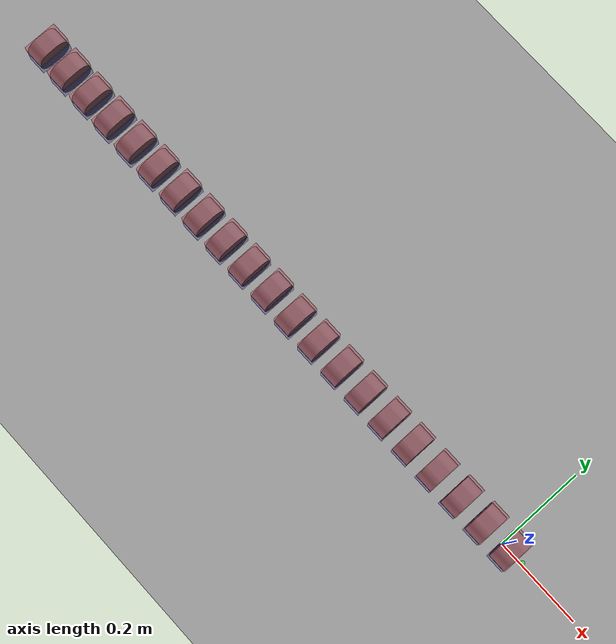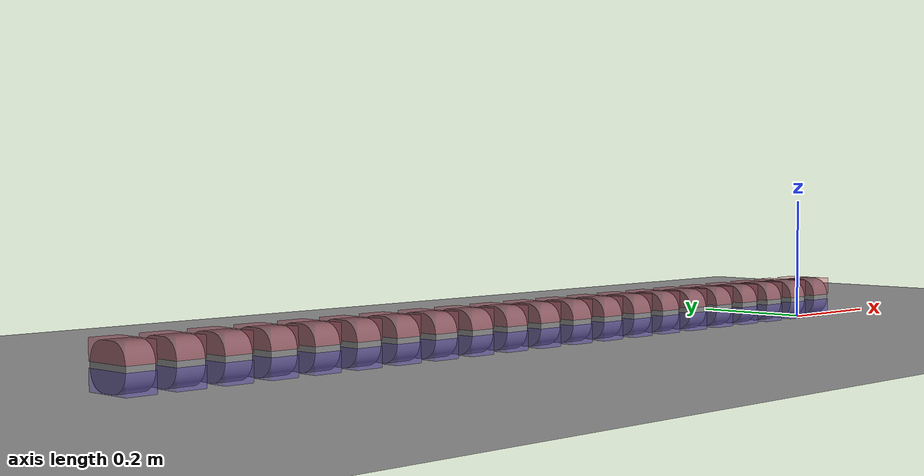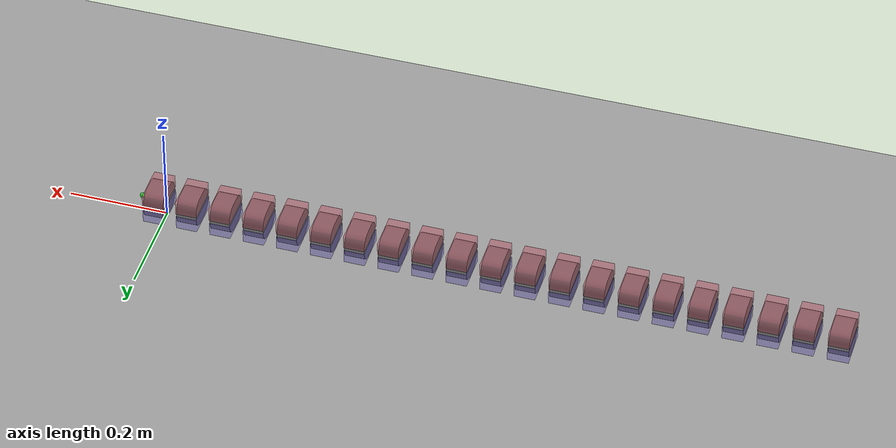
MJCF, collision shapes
<mujoco model="Horcrux v2 n20 with flat plane">
    <include file="horcrux_n20.xml"/>
    <option timestep="0.005"/>

    <asset>
        <texture type="skybox" builtin="gradient" width="512" height="512" rgb1=".4 .6 .8" rgb2="0 0 0"/>
        <texture name="texgeom" type="cube" builtin="flat" mark="cross" width="128" height="128"
                 rgb1="0.6 0.6 0.6" rgb2="0.6 0.6 0.6" markrgb="1 1 1"/>
        <texture name="texplane" type="2d" builtin="checker" rgb1=".55 .55 .55" rgb2=".75 .75 .75"
                 width="512" height="512"/>
        <material name="MatPlane" reflectance="0.0" texture="texplane" texrepeat="1 1" texuniform="true"
                  rgba="1 1 1 1"/>
        <material name="capsule" texture="texgeom" texuniform="true" rgba=".4 .9 .6 1" />
        <material name="ellipsoid" texture="texgeom" texuniform="true" rgba=".4 .6 .9 1" />
        <material name="box" texture="texgeom" texuniform="true" rgba=".4 .9 .9 1" />
        <material name="cylinder" texture="texgeom" texuniform="true" rgba=".8 .6 .8 1" />
        <material name="sphere" texture="texgeom" texuniform="true" rgba=".9 .1 .1 1" />
    </asset>

<worldbody>
    <geom name="floor" type="plane" size="30 30 .5" priority="2" friction="0.65 0.015 0.01" material="MatPlane"/>
</worldbody>

</mujoco>

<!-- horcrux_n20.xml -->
<mujoco model="Horcrux v2 body n20">
    <!-- AUTO-GENERATED by generate_scalable_mjcf.py (n=20 joints). DO NOT EDIT — regenerate instead. Source: resources/horcrux_p.xml -->
    <asset>
        <mesh name="link_collision" file="../resources/assets/link_collision_mesh.STL" />
        <material name="black_medium_gloss_plastic" specular="1.0" shininess="0.099901085" rgba="0.101961 0.101961 0.101961 1.000000" />
        <material name="black_spray_paint" specular="1.0" shininess="0.001136835" rgba="0.058824 0.058824 0.058824 1.000000" />
        <material name="brushed_nickel" specular="1.0" shininess="0.006954886" rgba="1.000000 0.960784 0.890196 1.000000" />
        <material name="color" specular="1.0" shininess="0.005212761999999999" rgba="0.000000 0.368627 0.094118 1.000000" />
        <material name="color-2" specular="1.0" shininess="0.005212761999999999" rgba="1.000000 1.000000 1.000000 1.000000" />
        <material name="color-3" specular="1.0" shininess="0.005212761999999999" rgba="0.250980 0.250980 0.250980 1.000000" />
        <material name="color-4" specular="1.0" shininess="0.005212761999999999" rgba="0.870588 0.709804 0.498039 1.000000" />
        <material name="color-5" specular="1.0" shininess="0.005212761999999999" rgba="0.749020 0.749020 0.749020 1.000000" />
        <material name="color-6" specular="1.0" shininess="0.005212761999999999" rgba="0.470588 0.431373 0.274510 1.000000" />
        <material name="color-7" specular="1.0" shininess="0.005212761999999999" rgba="0.247059 0.247059 0.247059 1.000000" />
        <material name="color-8" specular="1.0" shininess="0.005212761999999999" rgba="0.929412 0.807843 0.764706 1.000000" />
        <material name="color-9" specular="1.0" shininess="0.005212761999999999" rgba="0.960784 0.960784 0.964706 1.000000" />
        <material name="frosted_plastic" specular="1.0" shininess="0.002559057" rgba="0.576471 0.929412 1.000000 1.000000" />
        <material name="frosted_plastic-2" specular="1.0" shininess="0.002559057" rgba="0.576471 0.929412 1.000000 1.000000" />
        <material name="frosted_plastic-3" specular="1.0" shininess="0.002559057" rgba="0.576471 0.929412 1.000000 1.000000" />
        <material name="light_grey_low_gloss_plastic" specular="1.0" shininess="0.001357886" rgba="0.498039 0.498039 0.498039 1.000000" />
        <material name="matte_rubber" specular="1.0" shininess="0.0012430000000000002" rgba="0.094118 0.078431 0.078431 1.000000" />
        <material name="satin_finish_aluminum" specular="1.0" shininess="0.003414631" rgba="0.866667 0.909804 1.000000 1.000000" />
        <material name="satin_finish_aluminum_(Cosmetic_Thread)" specular="1.0" shininess="0.003414631" rgba="0.866667 0.909804 1.000000 1.000000" />
        <mesh file="../resources/assets/head_0.obj" />
        <mesh file="../resources/assets/head_1.obj" />
        <mesh file="../resources/assets/head_2.obj" />
        <mesh file="../resources/assets/head_3.obj" />
        <mesh file="../resources/assets/head_4.obj" />
        <mesh file="../resources/assets/head_5.obj" />
        <mesh file="../resources/assets/head_6.obj" />
        <mesh file="../resources/assets/head_7.obj" />
        <mesh file="../resources/assets/head_8.obj" />
        <mesh file="../resources/assets/head_9.obj" />
        <mesh file="../resources/assets/head_10.obj" />
        <mesh file="../resources/assets/head_11.obj" />
        <mesh file="../resources/assets/head_12.obj" />
        <mesh file="../resources/assets/head_13.obj" />
        <mesh file="../resources/assets/head_14.obj" />
        <mesh file="../resources/assets/head_15.obj" />
        <mesh file="../resources/assets/head_16.obj" />
        <mesh file="../resources/assets/head_17.obj" />
        <mesh file="../resources/assets/head_18.obj" />
        <material name="v-color" specular="1.0" shininess="0.005212761999999999" rgba="0.247059 0.247059 0.247059 1.000000" />
        <material name="v-color-10" specular="1.0" shininess="0.005212761999999999" rgba="0.749020 0.749020 0.749020 1.000000" />
        <material name="v-color-2" specular="1.0" shininess="0.005212761999999999" rgba="0.929412 0.807843 0.764706 1.000000" />
        <material name="v-color-3" specular="1.0" shininess="0.005212761999999999" rgba="0.960784 0.960784 0.964706 1.000000" />
        <material name="v-color-4" specular="1.0" shininess="0.005212761999999999" rgba="0.117647 0.294118 0.031373 1.000000" />
        <material name="v-color-5" specular="1.0" shininess="0.005212761999999999" rgba="0.470588 0.431373 0.274510 1.000000" />
        <material name="v-color-7" specular="1.0" shininess="0.005212761999999999" rgba="1.000000 1.000000 1.000000 1.000000" />
        <material name="v-color-8" specular="1.0" shininess="0.005212761999999999" rgba="0.250980 0.250980 0.250980 1.000000" />
        <material name="v-color-9" specular="1.0" shininess="0.005212761999999999" rgba="0.870588 0.709804 0.498039 1.000000" />
        <material name="glossy_rubber" specular="1.0" shininess="0.005212761999999999" rgba="0.298039 0.298039 0.298039 1.000000" />
        <mesh file="../resources/assets/v-link_0.obj" />
        <mesh file="../resources/assets/v-link_1.obj" />
        <mesh file="../resources/assets/v-link_2.obj" />
        <mesh file="../resources/assets/v-link_3.obj" />
        <mesh file="../resources/assets/v-link_4.obj" />
        <mesh file="../resources/assets/v-link_5.obj" />
        <mesh file="../resources/assets/v-link_6.obj" />
        <mesh file="../resources/assets/v-link_7.obj" />
        <mesh file="../resources/assets/v-link_8.obj" />
        <mesh file="../resources/assets/v-link_9.obj" />
        <mesh file="../resources/assets/v-link_10.obj" />
        <mesh file="../resources/assets/v-link_11.obj" />
        <mesh file="../resources/assets/v-link_12.obj" />
        <mesh file="../resources/assets/v-link_13.obj" />
        <mesh file="../resources/assets/v-link_14.obj" />
        <mesh file="../resources/assets/v-link_15.obj" />
        <mesh file="../resources/assets/v-link_16.obj" />
        <mesh file="../resources/assets/v-link_17.obj" />
        <mesh file="../resources/assets/v-link_18.obj" />
        <material name="black_medium_gloss_plastic.001" specular="1.0" shininess="0.099901085" rgba="0.101961 0.101961 0.101961 1.000000" />
        <material name="black_spray_paint.001" specular="1.0" shininess="0.001136835" rgba="0.058824 0.058824 0.058824 1.000000" />
        <material name="brushed_nickel.001" specular="1.0" shininess="0.006954886" rgba="1.000000 0.960784 0.890196 1.000000" />
        <material name="color-2.001" specular="1.0" shininess="0.005212761999999999" rgba="1.000000 1.000000 1.000000 1.000000" />
        <material name="color-3.001" specular="1.0" shininess="0.005212761999999999" rgba="0.250980 0.250980 0.250980 1.000000" />
        <material name="color-4.001" specular="1.0" shininess="0.005212761999999999" rgba="0.870588 0.709804 0.498039 1.000000" />
        <material name="color-5.001" specular="1.0" shininess="0.005212761999999999" rgba="0.749020 0.749020 0.749020 1.000000" />
        <material name="color-6.001" specular="1.0" shininess="0.005212761999999999" rgba="0.470588 0.431373 0.274510 1.000000" />
        <material name="color-7.001" specular="1.0" shininess="0.005212761999999999" rgba="0.247059 0.247059 0.247059 1.000000" />
        <material name="color-8.001" specular="1.0" shininess="0.005212761999999999" rgba="0.929412 0.807843 0.764706 1.000000" />
        <material name="color-9.001" specular="1.0" shininess="0.005212761999999999" rgba="0.960784 0.960784 0.964706 1.000000" />
        <material name="color.001" specular="1.0" shininess="0.005212761999999999" rgba="0.117647 0.294118 0.031373 1.000000" />
        <material name="frosted_plastic-2.001" specular="1.0" shininess="0.002559057" rgba="0.576471 0.929412 1.000000 1.000000" />
        <material name="frosted_plastic-3.001" specular="1.0" shininess="0.002559057" rgba="0.576471 0.929412 1.000000 1.000000" />
        <material name="frosted_plastic.001" specular="1.0" shininess="0.002559057" rgba="0.576471 0.929412 1.000000 1.000000" />
        <material name="glossy_rubber.001" specular="1.0" shininess="0.005212761999999999" rgba="0.298039 0.298039 0.298039 1.000000" />
        <material name="light_grey_low_gloss_plastic.001" specular="1.0" shininess="0.001357886" rgba="0.498039 0.498039 0.498039 1.000000" />
        <material name="satin_finish_aluminum.001" specular="1.0" shininess="0.003414631" rgba="0.866667 0.909804 1.000000 1.000000" />
        <material name="satin_finish_aluminum_(Cosmetic_Thread).001" specular="1.0" shininess="0.003414631" rgba="0.866667 0.909804 1.000000 1.000000" />
        <mesh file="../resources/assets/h-link_0.obj" />
        <mesh file="../resources/assets/h-link_1.obj" />
        <mesh file="../resources/assets/h-link_2.obj" />
        <mesh file="../resources/assets/h-link_3.obj" />
        <mesh file="../resources/assets/h-link_4.obj" />
        <mesh file="../resources/assets/h-link_5.obj" />
        <mesh file="../resources/assets/h-link_6.obj" />
        <mesh file="../resources/assets/h-link_7.obj" />
        <mesh file="../resources/assets/h-link_8.obj" />
        <mesh file="../resources/assets/h-link_9.obj" />
        <mesh file="../resources/assets/h-link_10.obj" />
        <mesh file="../resources/assets/h-link_11.obj" />
        <mesh file="../resources/assets/h-link_12.obj" />
        <mesh file="../resources/assets/h-link_13.obj" />
        <mesh file="../resources/assets/h-link_14.obj" />
        <mesh file="../resources/assets/h-link_15.obj" />
        <mesh file="../resources/assets/h-link_16.obj" />
        <mesh file="../resources/assets/h-link_17.obj" />
        <mesh file="../resources/assets/h-link_18.obj" />
    </asset>
    <default>
        <motor ctrlrange="-3 3" ctrllimited="true" />
        <default class="joint_defaults">
            <joint type="hinge" pos="0.0685 0 0" limited="true" range="-45 45" damping="0.13" armature="0.01" />
        </default>
        <default class="collision-mesh">
            <geom group="3" type="mesh" mesh="link_collision" mass="0.165" condim="4" rgba="0.5 0.5 0.5 0.1" priority="1" friction="0.7 0.015 0.001" euler="90 90 0" />
        </default>
        <default class="visual">
            <geom group="2" type="mesh" mass="0" contype="0" conaffinity="0" />
        </default>
        <default class="collision">
            <geom group="3" type="mesh" />
        </default>
    </default>
    <visual>
        <map force="0.1" zfar="30" />
        <rgba haze="0.15 0.25 0.35 1" />
        <quality shadowsize="4096" />
        <global offwidth="1280" offheight="1280" />
    </visual>
    <worldbody>
        <body>
            <camera name="ceiling" mode="fixed" fovy="48" pos="-0.5 0 3.5" euler="0 0 0" />
        </body>
        <body name="link1" pos="0 0 0.035" euler="0 0 0">
            <freejoint name="root" />
            <site name="s_tool" pos="0.05 0 0.0" euler="0 0 0" rgba="0.2 0.9 0.3 1" />
            <site name="s_link1_top" type="box" size="0.021 0.038 0.014" pos="0.016 0 0.018" rgba="0.8 0.1 0.2 0.3" />
            <site name="s_link1_bot" type="box" size="0.021 0.038 0.014" pos="0.016 0 -0.018" rgba="0.2 0.1 0.8 0.3" />
            <geom name="collision-link1" class="collision-mesh" />
            <geom mesh="head_0" pos="0 0 -0.03125" euler="0 90 90" material="matte_rubber" class="visual" />
            <geom mesh="head_1" pos="0 0 -0.03125" euler="0 90 90" material="color-9" class="visual" />
            <geom mesh="head_2" pos="0 0 -0.03125" euler="0 90 90" material="color-8" class="visual" />
            <geom mesh="head_3" pos="0 0 -0.03125" euler="0 90 90" material="color-7" class="visual" />
            <geom mesh="head_4" pos="0 0 -0.03125" euler="0 90 90" material="color-6" class="visual" />
            <geom mesh="head_5" pos="0 0 -0.03125" euler="0 90 90" material="color-5" class="visual" />
            <geom mesh="head_6" pos="0 0 -0.03125" euler="0 90 90" material="color-4" class="visual" />
            <geom mesh="head_7" pos="0 0 -0.03125" euler="0 90 90" material="color-3" class="visual" />
            <geom mesh="head_8" pos="0 0 -0.03125" euler="0 90 90" material="color-2" class="visual" />
            <geom mesh="head_9" pos="0 0 -0.03125" euler="0 90 90" material="color" class="visual" />
            <geom mesh="head_10" pos="0 0 -0.03125" euler="0 90 90" material="light_grey_low_gloss_plastic" class="visual" />
            <geom mesh="head_11" pos="0 0 -0.03125" euler="0 90 90" material="frosted_plastic-3" class="visual" />
            <geom mesh="head_12" pos="0 0 -0.03125" euler="0 90 90" material="frosted_plastic-2" class="visual" />
            <geom mesh="head_13" pos="0 0 -0.03125" euler="0 90 90" material="frosted_plastic" class="visual" />
            <geom mesh="head_14" pos="0 0 -0.03125" euler="0 90 90" material="satin_finish_aluminum_(Cosmetic_Thread)" class="visual" />
            <geom mesh="head_15" pos="0 0 -0.03125" euler="0 90 90" material="satin_finish_aluminum" class="visual" />
            <geom mesh="head_16" pos="0 0 -0.03125" euler="0 90 90" material="black_medium_gloss_plastic" class="visual" />
            <geom mesh="head_17" pos="0 0 -0.03125" euler="0 90 90" material="brushed_nickel" class="visual" />
            <geom mesh="head_18" pos="0 0 -0.03125" euler="0 90 90" material="black_spray_paint" class="visual" />
            <body name="link2" pos="-0.0685 0 0" euler="0 0 0">
                <joint class="joint_defaults" name="joint1" axis="0 1 0" />
                <site name="s_link2_top" type="box" size="0.021 0.038 0.014" pos="0.016 0 0.018" rgba="0.8 0.1 0.2 0.3" />
                <site name="s_link2_bot" type="box" size="0.021 0.038 0.014" pos="0.016 0 -0.018" rgba="0.2 0.1 0.8 0.3" />
                <geom name="collision-link2" class="collision-mesh" />
                <geom mesh="h-link_0" pos="0 0 -0.03125" euler="0 90 90" material="glossy_rubber" class="visual" />
                <geom mesh="h-link_1" pos="0 0 -0.03125" euler="0 90 90" material="v-color-10" class="visual" />
                <geom mesh="h-link_2" pos="0 0 -0.03125" euler="0 90 90" material="v-color-9" class="visual" />
                <geom mesh="h-link_3" pos="0 0 -0.03125" euler="0 90 90" material="v-color-8" class="visual" />
                <geom mesh="h-link_4" pos="0 0 -0.03125" euler="0 90 90" material="v-color-7" class="visual" />
                <geom mesh="h-link_5" pos="0 0 -0.03125" euler="0 90 90" material="v-color-5" class="visual" />
                <geom mesh="h-link_6" pos="0 0 -0.03125" euler="0 90 90" material="v-color-4" class="visual" />
                <geom mesh="h-link_7" pos="0 0 -0.03125" euler="0 90 90" material="v-color-3" class="visual" />
                <geom mesh="h-link_8" pos="0 0 -0.03125" euler="0 90 90" material="v-color-2" class="visual" />
                <geom mesh="h-link_9" pos="0 0 -0.03125" euler="0 90 90" material="v-color" class="visual" />
                <geom mesh="h-link_10" pos="0 0 -0.03125" euler="0 90 90" material="light_grey_low_gloss_plastic" class="visual" />
                <geom mesh="h-link_11" pos="0 0 -0.03125" euler="0 90 90" material="frosted_plastic-3" class="visual" />
                <geom mesh="h-link_12" pos="0 0 -0.03125" euler="0 90 90" material="frosted_plastic-2" class="visual" />
                <geom mesh="h-link_13" pos="0 0 -0.03125" euler="0 90 90" material="frosted_plastic" class="visual" />
                <geom mesh="h-link_14" pos="0 0 -0.03125" euler="0 90 90" material="satin_finish_aluminum_(Cosmetic_Thread)" class="visual" />
                <geom mesh="h-link_15" pos="0 0 -0.03125" euler="0 90 90" material="satin_finish_aluminum" class="visual" />
                <geom mesh="h-link_16" pos="0 0 -0.03125" euler="0 90 90" material="black_medium_gloss_plastic" class="visual" />
                <geom mesh="h-link_17" pos="0 0 -0.03125" euler="0 90 90" material="brushed_nickel" class="visual" />
                <geom mesh="h-link_18" pos="0 0 -0.03125" euler="0 90 90" material="black_spray_paint" class="visual" />
                <body name="link3" pos="-0.0685 0 0" euler="0 0 0">
                    <joint class="joint_defaults" name="joint2" axis="0 0 1" />
                    <site name="s_link3_top" type="box" size="0.021 0.038 0.014" pos="0.016 0 0.018" rgba="0.8 0.1 0.2 0.3" />
                    <site name="s_link3_bot" type="box" size="0.021 0.038 0.014" pos="0.016 0 -0.018" rgba="0.2 0.1 0.8 0.3" />
                    <geom name="collision-link3" class="collision-mesh" />
                    <geom mesh="v-link_0" pos="0 0 -0.03125" euler="0 90 90" material="glossy_rubber" class="visual" />
                    <geom mesh="v-link_1" pos="0 0 -0.03125" euler="0 90 90" material="v-color-10" class="visual" />
                    <geom mesh="v-link_2" pos="0 0 -0.03125" euler="0 90 90" material="v-color-9" class="visual" />
                    <geom mesh="v-link_3" pos="0 0 -0.03125" euler="0 90 90" material="v-color-8" class="visual" />
                    <geom mesh="v-link_4" pos="0 0 -0.03125" euler="0 90 90" material="v-color-7" class="visual" />
                    <geom mesh="v-link_5" pos="0 0 -0.03125" euler="0 90 90" material="v-color-5" class="visual" />
                    <geom mesh="v-link_6" pos="0 0 -0.03125" euler="0 90 90" material="v-color-4" class="visual" />
                    <geom mesh="v-link_7" pos="0 0 -0.03125" euler="0 90 90" material="v-color-3" class="visual" />
                    <geom mesh="v-link_8" pos="0 0 -0.03125" euler="0 90 90" material="v-color-2" class="visual" />
                    <geom mesh="v-link_9" pos="0 0 -0.03125" euler="0 90 90" material="v-color" class="visual" />
                    <geom mesh="v-link_10" pos="0 0 -0.03125" euler="0 90 90" material="light_grey_low_gloss_plastic" class="visual" />
                    <geom mesh="v-link_11" pos="0 0 -0.03125" euler="0 90 90" material="frosted_plastic-3" class="visual" />
                    <geom mesh="v-link_12" pos="0 0 -0.03125" euler="0 90 90" material="frosted_plastic-2" class="visual" />
                    <geom mesh="v-link_13" pos="0 0 -0.03125" euler="0 90 90" material="frosted_plastic" class="visual" />
                    <geom mesh="v-link_14" pos="0 0 -0.03125" euler="0 90 90" material="satin_finish_aluminum_(Cosmetic_Thread)" class="visual" />
                    <geom mesh="v-link_15" pos="0 0 -0.03125" euler="0 90 90" material="satin_finish_aluminum" class="visual" />
                    <geom mesh="v-link_16" pos="0 0 -0.03125" euler="0 90 90" material="black_medium_gloss_plastic" class="visual" />
                    <geom mesh="v-link_17" pos="0 0 -0.03125" euler="0 90 90" material="brushed_nickel" class="visual" />
                    <geom mesh="v-link_18" pos="0 0 -0.03125" euler="0 90 90" material="black_spray_paint" class="visual" />
                    <body name="link4" pos="-0.0685 0 0" euler="0 0 0">
                        <joint class="joint_defaults" name="joint3" axis="0 1 0" />
                        <site name="s_link4_top" type="box" size="0.021 0.038 0.014" pos="0.016 0 0.018" rgba="0.8 0.1 0.2 0.3" />
                        <site name="s_link4_bot" type="box" size="0.021 0.038 0.014" pos="0.016 0 -0.018" rgba="0.2 0.1 0.8 0.3" />
                        <geom name="collision-link4" class="collision-mesh" />
                        <geom mesh="h-link_0" pos="0 0 -0.03125" euler="0 90 90" material="glossy_rubber" class="visual" />
                        <geom mesh="h-link_1" pos="0 0 -0.03125" euler="0 90 90" material="v-color-10" class="visual" />
                        <geom mesh="h-link_2" pos="0 0 -0.03125" euler="0 90 90" material="v-color-9" class="visual" />
                        <geom mesh="h-link_3" pos="0 0 -0.03125" euler="0 90 90" material="v-color-8" class="visual" />
                        <geom mesh="h-link_4" pos="0 0 -0.03125" euler="0 90 90" material="v-color-7" class="visual" />
                        <geom mesh="h-link_5" pos="0 0 -0.03125" euler="0 90 90" material="v-color-5" class="visual" />
                        <geom mesh="h-link_6" pos="0 0 -0.03125" euler="0 90 90" material="v-color-4" class="visual" />
                        <geom mesh="h-link_7" pos="0 0 -0.03125" euler="0 90 90" material="v-color-3" class="visual" />
                        <geom mesh="h-link_8" pos="0 0 -0.03125" euler="0 90 90" material="v-color-2" class="visual" />
                        <geom mesh="h-link_9" pos="0 0 -0.03125" euler="0 90 90" material="v-color" class="visual" />
                        <geom mesh="h-link_10" pos="0 0 -0.03125" euler="0 90 90" material="light_grey_low_gloss_plastic" class="visual" />
                        <geom mesh="h-link_11" pos="0 0 -0.03125" euler="0 90 90" material="frosted_plastic-3" class="visual" />
                        <geom mesh="h-link_12" pos="0 0 -0.03125" euler="0 90 90" material="frosted_plastic-2" class="visual" />
                        <geom mesh="h-link_13" pos="0 0 -0.03125" euler="0 90 90" material="frosted_plastic" class="visual" />
                        <geom mesh="h-link_14" pos="0 0 -0.03125" euler="0 90 90" material="satin_finish_aluminum_(Cosmetic_Thread)" class="visual" />
                        <geom mesh="h-link_15" pos="0 0 -0.03125" euler="0 90 90" material="satin_finish_aluminum" class="visual" />
                        <geom mesh="h-link_16" pos="0 0 -0.03125" euler="0 90 90" material="black_medium_gloss_plastic" class="visual" />
                        <geom mesh="h-link_17" pos="0 0 -0.03125" euler="0 90 90" material="brushed_nickel" class="visual" />
                        <geom mesh="h-link_18" pos="0 0 -0.03125" euler="0 90 90" material="black_spray_paint" class="visual" />
                        <body name="link5" pos="-0.0685 0 0" euler="0 0 0">
                            <joint class="joint_defaults" name="joint4" axis="0 0 1" />
                            <site name="s_link5_top" type="box" size="0.021 0.038 0.014" pos="0.016 0 0.018" rgba="0.8 0.1 0.2 0.3" />
                            <site name="s_link5_bot" type="box" size="0.021 0.038 0.014" pos="0.016 0 -0.018" rgba="0.2 0.1 0.8 0.3" />
                            <geom name="collision-link5" class="collision-mesh" />
                            <geom mesh="v-link_0" pos="0 0 -0.03125" euler="0 90 90" material="glossy_rubber" class="visual" />
                            <geom mesh="v-link_1" pos="0 0 -0.03125" euler="0 90 90" material="v-color-10" class="visual" />
                            <geom mesh="v-link_2" pos="0 0 -0.03125" euler="0 90 90" material="v-color-9" class="visual" />
                            <geom mesh="v-link_3" pos="0 0 -0.03125" euler="0 90 90" material="v-color-8" class="visual" />
                            <geom mesh="v-link_4" pos="0 0 -0.03125" euler="0 90 90" material="v-color-7" class="visual" />
                            <geom mesh="v-link_5" pos="0 0 -0.03125" euler="0 90 90" material="v-color-5" class="visual" />
                            <geom mesh="v-link_6" pos="0 0 -0.03125" euler="0 90 90" material="v-color-4" class="visual" />
                            <geom mesh="v-link_7" pos="0 0 -0.03125" euler="0 90 90" material="v-color-3" class="visual" />
                            <geom mesh="v-link_8" pos="0 0 -0.03125" euler="0 90 90" material="v-color-2" class="visual" />
                            <geom mesh="v-link_9" pos="0 0 -0.03125" euler="0 90 90" material="v-color" class="visual" />
                            <geom mesh="v-link_10" pos="0 0 -0.03125" euler="0 90 90" material="light_grey_low_gloss_plastic" class="visual" />
                            <geom mesh="v-link_11" pos="0 0 -0.03125" euler="0 90 90" material="frosted_plastic-3" class="visual" />
                            <geom mesh="v-link_12" pos="0 0 -0.03125" euler="0 90 90" material="frosted_plastic-2" class="visual" />
                            <geom mesh="v-link_13" pos="0 0 -0.03125" euler="0 90 90" material="frosted_plastic" class="visual" />
                            <geom mesh="v-link_14" pos="0 0 -0.03125" euler="0 90 90" material="satin_finish_aluminum_(Cosmetic_Thread)" class="visual" />
                            <geom mesh="v-link_15" pos="0 0 -0.03125" euler="0 90 90" material="satin_finish_aluminum" class="visual" />
                            <geom mesh="v-link_16" pos="0 0 -0.03125" euler="0 90 90" material="black_medium_gloss_plastic" class="visual" />
                            <geom mesh="v-link_17" pos="0 0 -0.03125" euler="0 90 90" material="brushed_nickel" class="visual" />
                            <geom mesh="v-link_18" pos="0 0 -0.03125" euler="0 90 90" material="black_spray_paint" class="visual" />
                            <body name="link6" pos="-0.0685 0 0" euler="0 0 0">
                                <joint class="joint_defaults" name="joint5" axis="0 1 0" />
                                <site name="s_link6_top" type="box" size="0.021 0.038 0.014" pos="0.016 0 0.018" rgba="0.8 0.1 0.2 0.3" />
                                <site name="s_link6_bot" type="box" size="0.021 0.038 0.014" pos="0.016 0 -0.018" rgba="0.2 0.1 0.8 0.3" />
                                <geom name="collision-link6" class="collision-mesh" />
                                <geom mesh="h-link_0" pos="0 0 -0.03125" euler="0 90 90" material="glossy_rubber" class="visual" />
                                <geom mesh="h-link_1" pos="0 0 -0.03125" euler="0 90 90" material="v-color-10" class="visual" />
                                <geom mesh="h-link_2" pos="0 0 -0.03125" euler="0 90 90" material="v-color-9" class="visual" />
                                <geom mesh="h-link_3" pos="0 0 -0.03125" euler="0 90 90" material="v-color-8" class="visual" />
                                <geom mesh="h-link_4" pos="0 0 -0.03125" euler="0 90 90" material="v-color-7" class="visual" />
                                <geom mesh="h-link_5" pos="0 0 -0.03125" euler="0 90 90" material="v-color-5" class="visual" />
                                <geom mesh="h-link_6" pos="0 0 -0.03125" euler="0 90 90" material="v-color-4" class="visual" />
                                <geom mesh="h-link_7" pos="0 0 -0.03125" euler="0 90 90" material="v-color-3" class="visual" />
                                <geom mesh="h-link_8" pos="0 0 -0.03125" euler="0 90 90" material="v-color-2" class="visual" />
                                <geom mesh="h-link_9" pos="0 0 -0.03125" euler="0 90 90" material="v-color" class="visual" />
                                <geom mesh="h-link_10" pos="0 0 -0.03125" euler="0 90 90" material="light_grey_low_gloss_plastic" class="visual" />
                                <geom mesh="h-link_11" pos="0 0 -0.03125" euler="0 90 90" material="frosted_plastic-3" class="visual" />
                                <geom mesh="h-link_12" pos="0 0 -0.03125" euler="0 90 90" material="frosted_plastic-2" class="visual" />
                                <geom mesh="h-link_13" pos="0 0 -0.03125" euler="0 90 90" material="frosted_plastic" class="visual" />
                                <geom mesh="h-link_14" pos="0 0 -0.03125" euler="0 90 90" material="satin_finish_aluminum_(Cosmetic_Thread)" class="visual" />
                                <geom mesh="h-link_15" pos="0 0 -0.03125" euler="0 90 90" material="satin_finish_aluminum" class="visual" />
                                <geom mesh="h-link_16" pos="0 0 -0.03125" euler="0 90 90" material="black_medium_gloss_plastic" class="visual" />
                                <geom mesh="h-link_17" pos="0 0 -0.03125" euler="0 90 90" material="brushed_nickel" class="visual" />
                                <geom mesh="h-link_18" pos="0 0 -0.03125" euler="0 90 90" material="black_spray_paint" class="visual" />
                                <body name="link7" pos="-0.0685 0 0" euler="0 0 0">
                                    <joint class="joint_defaults" name="joint6" axis="0 0 1" />
                                    <site name="s_link7_top" type="box" size="0.021 0.038 0.014" pos="0.016 0 0.018" rgba="0.8 0.1 0.2 0.3" />
                                    <site name="s_link7_bot" type="box" size="0.021 0.038 0.014" pos="0.016 0 -0.018" rgba="0.2 0.1 0.8 0.3" />
                                    <geom name="collision-link7" class="collision-mesh" />
                                    <geom mesh="v-link_0" pos="0 0 -0.03125" euler="0 90 90" material="glossy_rubber" class="visual" />
                                    <geom mesh="v-link_1" pos="0 0 -0.03125" euler="0 90 90" material="v-color-10" class="visual" />
                                    <geom mesh="v-link_2" pos="0 0 -0.03125" euler="0 90 90" material="v-color-9" class="visual" />
                                    <geom mesh="v-link_3" pos="0 0 -0.03125" euler="0 90 90" material="v-color-8" class="visual" />
                                    <geom mesh="v-link_4" pos="0 0 -0.03125" euler="0 90 90" material="v-color-7" class="visual" />
                                    <geom mesh="v-link_5" pos="0 0 -0.03125" euler="0 90 90" material="v-color-5" class="visual" />
                                    <geom mesh="v-link_6" pos="0 0 -0.03125" euler="0 90 90" material="v-color-4" class="visual" />
                                    <geom mesh="v-link_7" pos="0 0 -0.03125" euler="0 90 90" material="v-color-3" class="visual" />
                                    <geom mesh="v-link_8" pos="0 0 -0.03125" euler="0 90 90" material="v-color-2" class="visual" />
                                    <geom mesh="v-link_9" pos="0 0 -0.03125" euler="0 90 90" material="v-color" class="visual" />
                                    <geom mesh="v-link_10" pos="0 0 -0.03125" euler="0 90 90" material="light_grey_low_gloss_plastic" class="visual" />
                                    <geom mesh="v-link_11" pos="0 0 -0.03125" euler="0 90 90" material="frosted_plastic-3" class="visual" />
                                    <geom mesh="v-link_12" pos="0 0 -0.03125" euler="0 90 90" material="frosted_plastic-2" class="visual" />
                                    <geom mesh="v-link_13" pos="0 0 -0.03125" euler="0 90 90" material="frosted_plastic" class="visual" />
                                    <geom mesh="v-link_14" pos="0 0 -0.03125" euler="0 90 90" material="satin_finish_aluminum_(Cosmetic_Thread)" class="visual" />
                                    <geom mesh="v-link_15" pos="0 0 -0.03125" euler="0 90 90" material="satin_finish_aluminum" class="visual" />
                                    <geom mesh="v-link_16" pos="0 0 -0.03125" euler="0 90 90" material="black_medium_gloss_plastic" class="visual" />
                                    <geom mesh="v-link_17" pos="0 0 -0.03125" euler="0 90 90" material="brushed_nickel" class="visual" />
                                    <geom mesh="v-link_18" pos="0 0 -0.03125" euler="0 90 90" material="black_spray_paint" class="visual" />
                                    <body name="link8" pos="-0.0685 0 0" euler="0 0 0">
                                        <joint class="joint_defaults" name="joint7" axis="0 1 0" />
                                        <site name="s_link8_top" type="box" size="0.021 0.038 0.014" pos="0.016 0 0.018" rgba="0.8 0.1 0.2 0.3" />
                                        <site name="s_link8_bot" type="box" size="0.021 0.038 0.014" pos="0.016 0 -0.018" rgba="0.2 0.1 0.8 0.3" />
                                        <geom name="collision-link8" class="collision-mesh" />
                                        <geom mesh="h-link_0" pos="0 0 -0.03125" euler="0 90 90" material="glossy_rubber" class="visual" />
                                        <geom mesh="h-link_1" pos="0 0 -0.03125" euler="0 90 90" material="v-color-10" class="visual" />
                                        <geom mesh="h-link_2" pos="0 0 -0.03125" euler="0 90 90" material="v-color-9" class="visual" />
                                        <geom mesh="h-link_3" pos="0 0 -0.03125" euler="0 90 90" material="v-color-8" class="visual" />
                                        <geom mesh="h-link_4" pos="0 0 -0.03125" euler="0 90 90" material="v-color-7" class="visual" />
                                        <geom mesh="h-link_5" pos="0 0 -0.03125" euler="0 90 90" material="v-color-5" class="visual" />
                                        <geom mesh="h-link_6" pos="0 0 -0.03125" euler="0 90 90" material="v-color-4" class="visual" />
                                        <geom mesh="h-link_7" pos="0 0 -0.03125" euler="0 90 90" material="v-color-3" class="visual" />
                                        <geom mesh="h-link_8" pos="0 0 -0.03125" euler="0 90 90" material="v-color-2" class="visual" />
                                        <geom mesh="h-link_9" pos="0 0 -0.03125" euler="0 90 90" material="v-color" class="visual" />
                                        <geom mesh="h-link_10" pos="0 0 -0.03125" euler="0 90 90" material="light_grey_low_gloss_plastic" class="visual" />
                                        <geom mesh="h-link_11" pos="0 0 -0.03125" euler="0 90 90" material="frosted_plastic-3" class="visual" />
                                        <geom mesh="h-link_12" pos="0 0 -0.03125" euler="0 90 90" material="frosted_plastic-2" class="visual" />
                                        <geom mesh="h-link_13" pos="0 0 -0.03125" euler="0 90 90" material="frosted_plastic" class="visual" />
                                        <geom mesh="h-link_14" pos="0 0 -0.03125" euler="0 90 90" material="satin_finish_aluminum_(Cosmetic_Thread)" class="visual" />
                                        <geom mesh="h-link_15" pos="0 0 -0.03125" euler="0 90 90" material="satin_finish_aluminum" class="visual" />
                                        <geom mesh="h-link_16" pos="0 0 -0.03125" euler="0 90 90" material="black_medium_gloss_plastic" class="visual" />
                                        <geom mesh="h-link_17" pos="0 0 -0.03125" euler="0 90 90" material="brushed_nickel" class="visual" />
                                        <geom mesh="h-link_18" pos="0 0 -0.03125" euler="0 90 90" material="black_spray_paint" class="visual" />
                                        <body name="link9" pos="-0.0685 0 0" euler="0 0 0">
                                            <joint class="joint_defaults" name="joint8" axis="0 0 1" />
                                            <site name="s_link9_top" type="box" size="0.021 0.038 0.014" pos="0.016 0 0.018" rgba="0.8 0.1 0.2 0.3" />
                                            <site name="s_link9_bot" type="box" size="0.021 0.038 0.014" pos="0.016 0 -0.018" rgba="0.2 0.1 0.8 0.3" />
                                            <geom name="collision-link9" class="collision-mesh" />
                                            <geom mesh="v-link_0" pos="0 0 -0.03125" euler="0 90 90" material="glossy_rubber" class="visual" />
                                            <geom mesh="v-link_1" pos="0 0 -0.03125" euler="0 90 90" material="v-color-10" class="visual" />
                                            <geom mesh="v-link_2" pos="0 0 -0.03125" euler="0 90 90" material="v-color-9" class="visual" />
                                            <geom mesh="v-link_3" pos="0 0 -0.03125" euler="0 90 90" material="v-color-8" class="visual" />
                                            <geom mesh="v-link_4" pos="0 0 -0.03125" euler="0 90 90" material="v-color-7" class="visual" />
                                            <geom mesh="v-link_5" pos="0 0 -0.03125" euler="0 90 90" material="v-color-5" class="visual" />
                                            <geom mesh="v-link_6" pos="0 0 -0.03125" euler="0 90 90" material="v-color-4" class="visual" />
                                            <geom mesh="v-link_7" pos="0 0 -0.03125" euler="0 90 90" material="v-color-3" class="visual" />
                                            <geom mesh="v-link_8" pos="0 0 -0.03125" euler="0 90 90" material="v-color-2" class="visual" />
                                            <geom mesh="v-link_9" pos="0 0 -0.03125" euler="0 90 90" material="v-color" class="visual" />
                                            <geom mesh="v-link_10" pos="0 0 -0.03125" euler="0 90 90" material="light_grey_low_gloss_plastic" class="visual" />
                                            <geom mesh="v-link_11" pos="0 0 -0.03125" euler="0 90 90" material="frosted_plastic-3" class="visual" />
                                            <geom mesh="v-link_12" pos="0 0 -0.03125" euler="0 90 90" material="frosted_plastic-2" class="visual" />
                                            <geom mesh="v-link_13" pos="0 0 -0.03125" euler="0 90 90" material="frosted_plastic" class="visual" />
                                            <geom mesh="v-link_14" pos="0 0 -0.03125" euler="0 90 90" material="satin_finish_aluminum_(Cosmetic_Thread)" class="visual" />
                                            <geom mesh="v-link_15" pos="0 0 -0.03125" euler="0 90 90" material="satin_finish_aluminum" class="visual" />
                                            <geom mesh="v-link_16" pos="0 0 -0.03125" euler="0 90 90" material="black_medium_gloss_plastic" class="visual" />
                                            <geom mesh="v-link_17" pos="0 0 -0.03125" euler="0 90 90" material="brushed_nickel" class="visual" />
                                            <geom mesh="v-link_18" pos="0 0 -0.03125" euler="0 90 90" material="black_spray_paint" class="visual" />
                                            <body name="link10" pos="-0.0685 0 0" euler="0 0 0">
                                                <joint class="joint_defaults" name="joint9" axis="0 1 0" />
                                                <site name="s_link10_top" type="box" size="0.021 0.038 0.014" pos="0.016 0 0.018" rgba="0.8 0.1 0.2 0.3" />
                                                <site name="s_link10_bot" type="box" size="0.021 0.038 0.014" pos="0.016 0 -0.018" rgba="0.2 0.1 0.8 0.3" />
                                                <geom name="collision-link10" class="collision-mesh" />
                                                <geom mesh="h-link_0" pos="0 0 -0.03125" euler="0 90 90" material="glossy_rubber" class="visual" />
                                                <geom mesh="h-link_1" pos="0 0 -0.03125" euler="0 90 90" material="v-color-10" class="visual" />
                                                <geom mesh="h-link_2" pos="0 0 -0.03125" euler="0 90 90" material="v-color-9" class="visual" />
                                                <geom mesh="h-link_3" pos="0 0 -0.03125" euler="0 90 90" material="v-color-8" class="visual" />
                                                <geom mesh="h-link_4" pos="0 0 -0.03125" euler="0 90 90" material="v-color-7" class="visual" />
                                                <geom mesh="h-link_5" pos="0 0 -0.03125" euler="0 90 90" material="v-color-5" class="visual" />
                                                <geom mesh="h-link_6" pos="0 0 -0.03125" euler="0 90 90" material="v-color-4" class="visual" />
                                                <geom mesh="h-link_7" pos="0 0 -0.03125" euler="0 90 90" material="v-color-3" class="visual" />
                                                <geom mesh="h-link_8" pos="0 0 -0.03125" euler="0 90 90" material="v-color-2" class="visual" />
                                                <geom mesh="h-link_9" pos="0 0 -0.03125" euler="0 90 90" material="v-color" class="visual" />
                                                <geom mesh="h-link_10" pos="0 0 -0.03125" euler="0 90 90" material="light_grey_low_gloss_plastic" class="visual" />
                                                <geom mesh="h-link_11" pos="0 0 -0.03125" euler="0 90 90" material="frosted_plastic-3" class="visual" />
                                                <geom mesh="h-link_12" pos="0 0 -0.03125" euler="0 90 90" material="frosted_plastic-2" class="visual" />
                                                <geom mesh="h-link_13" pos="0 0 -0.03125" euler="0 90 90" material="frosted_plastic" class="visual" />
                                                <geom mesh="h-link_14" pos="0 0 -0.03125" euler="0 90 90" material="satin_finish_aluminum_(Cosmetic_Thread)" class="visual" />
                                                <geom mesh="h-link_15" pos="0 0 -0.03125" euler="0 90 90" material="satin_finish_aluminum" class="visual" />
                                                <geom mesh="h-link_16" pos="0 0 -0.03125" euler="0 90 90" material="black_medium_gloss_plastic" class="visual" />
                                                <geom mesh="h-link_17" pos="0 0 -0.03125" euler="0 90 90" material="brushed_nickel" class="visual" />
                                                <geom mesh="h-link_18" pos="0 0 -0.03125" euler="0 90 90" material="black_spray_paint" class="visual" />
                                                <body name="link11" pos="-0.0685 0 0" euler="0 0 0">
                                                    <joint class="joint_defaults" name="joint10" axis="0 0 1" />
                                                    <site name="s_link11_top" type="box" size="0.021 0.038 0.014" pos="0.016 0 0.018" rgba="0.8 0.1 0.2 0.3" />
                                                    <site name="s_link11_bot" type="box" size="0.021 0.038 0.014" pos="0.016 0 -0.018" rgba="0.2 0.1 0.8 0.3" />
                                                    <geom name="collision-link11" class="collision-mesh" />
                                                    <geom mesh="v-link_0" pos="0 0 -0.03125" euler="0 90 90" material="glossy_rubber" class="visual" />
                                                    <geom mesh="v-link_1" pos="0 0 -0.03125" euler="0 90 90" material="v-color-10" class="visual" />
                                                    <geom mesh="v-link_2" pos="0 0 -0.03125" euler="0 90 90" material="v-color-9" class="visual" />
                                                    <geom mesh="v-link_3" pos="0 0 -0.03125" euler="0 90 90" material="v-color-8" class="visual" />
                                                    <geom mesh="v-link_4" pos="0 0 -0.03125" euler="0 90 90" material="v-color-7" class="visual" />
                                                    <geom mesh="v-link_5" pos="0 0 -0.03125" euler="0 90 90" material="v-color-5" class="visual" />
                                                    <geom mesh="v-link_6" pos="0 0 -0.03125" euler="0 90 90" material="v-color-4" class="visual" />
                                                    <geom mesh="v-link_7" pos="0 0 -0.03125" euler="0 90 90" material="v-color-3" class="visual" />
                                                    <geom mesh="v-link_8" pos="0 0 -0.03125" euler="0 90 90" material="v-color-2" class="visual" />
                                                    <geom mesh="v-link_9" pos="0 0 -0.03125" euler="0 90 90" material="v-color" class="visual" />
                                                    <geom mesh="v-link_10" pos="0 0 -0.03125" euler="0 90 90" material="light_grey_low_gloss_plastic" class="visual" />
                                                    <geom mesh="v-link_11" pos="0 0 -0.03125" euler="0 90 90" material="frosted_plastic-3" class="visual" />
                                                    <geom mesh="v-link_12" pos="0 0 -0.03125" euler="0 90 90" material="frosted_plastic-2" class="visual" />
                                                    <geom mesh="v-link_13" pos="0 0 -0.03125" euler="0 90 90" material="frosted_plastic" class="visual" />
                                                    <geom mesh="v-link_14" pos="0 0 -0.03125" euler="0 90 90" material="satin_finish_aluminum_(Cosmetic_Thread)" class="visual" />
                                                    <geom mesh="v-link_15" pos="0 0 -0.03125" euler="0 90 90" material="satin_finish_aluminum" class="visual" />
                                                    <geom mesh="v-link_16" pos="0 0 -0.03125" euler="0 90 90" material="black_medium_gloss_plastic" class="visual" />
                                                    <geom mesh="v-link_17" pos="0 0 -0.03125" euler="0 90 90" material="brushed_nickel" class="visual" />
                                                    <geom mesh="v-link_18" pos="0 0 -0.03125" euler="0 90 90" material="black_spray_paint" class="visual" />
                                                    <body name="link12" pos="-0.0685 0 0" euler="0 0 0">
                                                        <joint class="joint_defaults" name="joint11" axis="0 1 0" />
                                                        <site name="s_link12_top" type="box" size="0.021 0.038 0.014" pos="0.016 0 0.018" rgba="0.8 0.1 0.2 0.3" />
                                                        <site name="s_link12_bot" type="box" size="0.021 0.038 0.014" pos="0.016 0 -0.018" rgba="0.2 0.1 0.8 0.3" />
                                                        <geom name="collision-link12" class="collision-mesh" />
                                                        <geom mesh="h-link_0" pos="0 0 -0.03125" euler="0 90 90" material="glossy_rubber" class="visual" />
                                                        <geom mesh="h-link_1" pos="0 0 -0.03125" euler="0 90 90" material="v-color-10" class="visual" />
                                                        <geom mesh="h-link_2" pos="0 0 -0.03125" euler="0 90 90" material="v-color-9" class="visual" />
                                                        <geom mesh="h-link_3" pos="0 0 -0.03125" euler="0 90 90" material="v-color-8" class="visual" />
                                                        <geom mesh="h-link_4" pos="0 0 -0.03125" euler="0 90 90" material="v-color-7" class="visual" />
                                                        <geom mesh="h-link_5" pos="0 0 -0.03125" euler="0 90 90" material="v-color-5" class="visual" />
                                                        <geom mesh="h-link_6" pos="0 0 -0.03125" euler="0 90 90" material="v-color-4" class="visual" />
                                                        <geom mesh="h-link_7" pos="0 0 -0.03125" euler="0 90 90" material="v-color-3" class="visual" />
                                                        <geom mesh="h-link_8" pos="0 0 -0.03125" euler="0 90 90" material="v-color-2" class="visual" />
                                                        <geom mesh="h-link_9" pos="0 0 -0.03125" euler="0 90 90" material="v-color" class="visual" />
                                                        <geom mesh="h-link_10" pos="0 0 -0.03125" euler="0 90 90" material="light_grey_low_gloss_plastic" class="visual" />
                                                        <geom mesh="h-link_11" pos="0 0 -0.03125" euler="0 90 90" material="frosted_plastic-3" class="visual" />
                                                        <geom mesh="h-link_12" pos="0 0 -0.03125" euler="0 90 90" material="frosted_plastic-2" class="visual" />
                                                        <geom mesh="h-link_13" pos="0 0 -0.03125" euler="0 90 90" material="frosted_plastic" class="visual" />
                                                        <geom mesh="h-link_14" pos="0 0 -0.03125" euler="0 90 90" material="satin_finish_aluminum_(Cosmetic_Thread)" class="visual" />
                                                        <geom mesh="h-link_15" pos="0 0 -0.03125" euler="0 90 90" material="satin_finish_aluminum" class="visual" />
                                                        <geom mesh="h-link_16" pos="0 0 -0.03125" euler="0 90 90" material="black_medium_gloss_plastic" class="visual" />
                                                        <geom mesh="h-link_17" pos="0 0 -0.03125" euler="0 90 90" material="brushed_nickel" class="visual" />
                                                        <geom mesh="h-link_18" pos="0 0 -0.03125" euler="0 90 90" material="black_spray_paint" class="visual" />
                                                        <body name="link13" pos="-0.0685 0 0" euler="0 0 0">
                                                            <joint class="joint_defaults" name="joint12" axis="0 0 1" />
                                                            <site name="s_link13_top" type="box" size="0.021 0.038 0.014" pos="0.016 0 0.018" rgba="0.8 0.1 0.2 0.3" />
                                                            <site name="s_link13_bot" type="box" size="0.021 0.038 0.014" pos="0.016 0 -0.018" rgba="0.2 0.1 0.8 0.3" />
                                                            <geom name="collision-link13" class="collision-mesh" />
                                                            <geom mesh="v-link_0" pos="0 0 -0.03125" euler="0 90 90" material="glossy_rubber" class="visual" />
                                                            <geom mesh="v-link_1" pos="0 0 -0.03125" euler="0 90 90" material="v-color-10" class="visual" />
                                                            <geom mesh="v-link_2" pos="0 0 -0.03125" euler="0 90 90" material="v-color-9" class="visual" />
                                                            <geom mesh="v-link_3" pos="0 0 -0.03125" euler="0 90 90" material="v-color-8" class="visual" />
                                                            <geom mesh="v-link_4" pos="0 0 -0.03125" euler="0 90 90" material="v-color-7" class="visual" />
                                                            <geom mesh="v-link_5" pos="0 0 -0.03125" euler="0 90 90" material="v-color-5" class="visual" />
                                                            <geom mesh="v-link_6" pos="0 0 -0.03125" euler="0 90 90" material="v-color-4" class="visual" />
                                                            <geom mesh="v-link_7" pos="0 0 -0.03125" euler="0 90 90" material="v-color-3" class="visual" />
                                                            <geom mesh="v-link_8" pos="0 0 -0.03125" euler="0 90 90" material="v-color-2" class="visual" />
                                                            <geom mesh="v-link_9" pos="0 0 -0.03125" euler="0 90 90" material="v-color" class="visual" />
                                                            <geom mesh="v-link_10" pos="0 0 -0.03125" euler="0 90 90" material="light_grey_low_gloss_plastic" class="visual" />
                                                            <geom mesh="v-link_11" pos="0 0 -0.03125" euler="0 90 90" material="frosted_plastic-3" class="visual" />
                                                            <geom mesh="v-link_12" pos="0 0 -0.03125" euler="0 90 90" material="frosted_plastic-2" class="visual" />
                                                            <geom mesh="v-link_13" pos="0 0 -0.03125" euler="0 90 90" material="frosted_plastic" class="visual" />
                                                            <geom mesh="v-link_14" pos="0 0 -0.03125" euler="0 90 90" material="satin_finish_aluminum_(Cosmetic_Thread)" class="visual" />
                                                            <geom mesh="v-link_15" pos="0 0 -0.03125" euler="0 90 90" material="satin_finish_aluminum" class="visual" />
                                                            <geom mesh="v-link_16" pos="0 0 -0.03125" euler="0 90 90" material="black_medium_gloss_plastic" class="visual" />
                                                            <geom mesh="v-link_17" pos="0 0 -0.03125" euler="0 90 90" material="brushed_nickel" class="visual" />
                                                            <geom mesh="v-link_18" pos="0 0 -0.03125" euler="0 90 90" material="black_spray_paint" class="visual" />
                                                            <body name="link14" pos="-0.0685 0 0" euler="0 0 0">
                                                                <joint class="joint_defaults" name="joint13" axis="0 1 0" />
                                                                <site name="s_link14_top" type="box" size="0.021 0.038 0.014" pos="0.016 0 0.018" rgba="0.8 0.1 0.2 0.3" />
                                                                <site name="s_link14_bot" type="box" size="0.021 0.038 0.014" pos="0.016 0 -0.018" rgba="0.2 0.1 0.8 0.3" />
                                                                <geom name="collision-link14" class="collision-mesh" />
                                                                <geom mesh="h-link_0" pos="0 0 -0.03125" euler="0 90 90" material="glossy_rubber" class="visual" />
                                                                <geom mesh="h-link_1" pos="0 0 -0.03125" euler="0 90 90" material="v-color-10" class="visual" />
                                                                <geom mesh="h-link_2" pos="0 0 -0.03125" euler="0 90 90" material="v-color-9" class="visual" />
                                                                <geom mesh="h-link_3" pos="0 0 -0.03125" euler="0 90 90" material="v-color-8" class="visual" />
                                                                <geom mesh="h-link_4" pos="0 0 -0.03125" euler="0 90 90" material="v-color-7" class="visual" />
                                                                <geom mesh="h-link_5" pos="0 0 -0.03125" euler="0 90 90" material="v-color-5" class="visual" />
                                                                <geom mesh="h-link_6" pos="0 0 -0.03125" euler="0 90 90" material="v-color-4" class="visual" />
                                                                <geom mesh="h-link_7" pos="0 0 -0.03125" euler="0 90 90" material="v-color-3" class="visual" />
                                                                <geom mesh="h-link_8" pos="0 0 -0.03125" euler="0 90 90" material="v-color-2" class="visual" />
                                                                <geom mesh="h-link_9" pos="0 0 -0.03125" euler="0 90 90" material="v-color" class="visual" />
                                                                <geom mesh="h-link_10" pos="0 0 -0.03125" euler="0 90 90" material="light_grey_low_gloss_plastic" class="visual" />
                                                                <geom mesh="h-link_11" pos="0 0 -0.03125" euler="0 90 90" material="frosted_plastic-3" class="visual" />
                                                                <geom mesh="h-link_12" pos="0 0 -0.03125" euler="0 90 90" material="frosted_plastic-2" class="visual" />
                                                                <geom mesh="h-link_13" pos="0 0 -0.03125" euler="0 90 90" material="frosted_plastic" class="visual" />
                                                                <geom mesh="h-link_14" pos="0 0 -0.03125" euler="0 90 90" material="satin_finish_aluminum_(Cosmetic_Thread)" class="visual" />
                                                                <geom mesh="h-link_15" pos="0 0 -0.03125" euler="0 90 90" material="satin_finish_aluminum" class="visual" />
                                                                <geom mesh="h-link_16" pos="0 0 -0.03125" euler="0 90 90" material="black_medium_gloss_plastic" class="visual" />
                                                                <geom mesh="h-link_17" pos="0 0 -0.03125" euler="0 90 90" material="brushed_nickel" class="visual" />
                                                                <geom mesh="h-link_18" pos="0 0 -0.03125" euler="0 90 90" material="black_spray_paint" class="visual" />
                                                                <body name="link15" pos="-0.0685 0 0" euler="0 0 0">
                                                                    <joint class="joint_defaults" name="joint14" axis="0 0 1" />
                                                                    <site name="s_link15_top" type="box" size="0.021 0.038 0.014" pos="0.016 0 0.018" rgba="0.8 0.1 0.2 0.3" />
                                                                    <site name="s_link15_bot" type="box" size="0.021 0.038 0.014" pos="0.016 0 -0.018" rgba="0.2 0.1 0.8 0.3" />
                                                                    <geom name="collision-link15" class="collision-mesh" />
                                                                    <geom mesh="v-link_0" pos="0 0 -0.03125" euler="0 90 90" material="glossy_rubber" class="visual" />
                                                                    <geom mesh="v-link_1" pos="0 0 -0.03125" euler="0 90 90" material="v-color-10" class="visual" />
                                                                    <geom mesh="v-link_2" pos="0 0 -0.03125" euler="0 90 90" material="v-color-9" class="visual" />
                                                                    <geom mesh="v-link_3" pos="0 0 -0.03125" euler="0 90 90" material="v-color-8" class="visual" />
                                                                    <geom mesh="v-link_4" pos="0 0 -0.03125" euler="0 90 90" material="v-color-7" class="visual" />
                                                                    <geom mesh="v-link_5" pos="0 0 -0.03125" euler="0 90 90" material="v-color-5" class="visual" />
                                                                    <geom mesh="v-link_6" pos="0 0 -0.03125" euler="0 90 90" material="v-color-4" class="visual" />
                                                                    <geom mesh="v-link_7" pos="0 0 -0.03125" euler="0 90 90" material="v-color-3" class="visual" />
                                                                    <geom mesh="v-link_8" pos="0 0 -0.03125" euler="0 90 90" material="v-color-2" class="visual" />
                                                                    <geom mesh="v-link_9" pos="0 0 -0.03125" euler="0 90 90" material="v-color" class="visual" />
                                                                    <geom mesh="v-link_10" pos="0 0 -0.03125" euler="0 90 90" material="light_grey_low_gloss_plastic" class="visual" />
                                                                    <geom mesh="v-link_11" pos="0 0 -0.03125" euler="0 90 90" material="frosted_plastic-3" class="visual" />
                                                                    <geom mesh="v-link_12" pos="0 0 -0.03125" euler="0 90 90" material="frosted_plastic-2" class="visual" />
                                                                    <geom mesh="v-link_13" pos="0 0 -0.03125" euler="0 90 90" material="frosted_plastic" class="visual" />
                                                                    <geom mesh="v-link_14" pos="0 0 -0.03125" euler="0 90 90" material="satin_finish_aluminum_(Cosmetic_Thread)" class="visual" />
                                                                    <geom mesh="v-link_15" pos="0 0 -0.03125" euler="0 90 90" material="satin_finish_aluminum" class="visual" />
                                                                    <geom mesh="v-link_16" pos="0 0 -0.03125" euler="0 90 90" material="black_medium_gloss_plastic" class="visual" />
                                                                    <geom mesh="v-link_17" pos="0 0 -0.03125" euler="0 90 90" material="brushed_nickel" class="visual" />
                                                                    <geom mesh="v-link_18" pos="0 0 -0.03125" euler="0 90 90" material="black_spray_paint" class="visual" />
                                                                    <body name="link16" pos="-0.0685 0 0" euler="0 0 0">
                                                                        <joint class="joint_defaults" name="joint15" axis="0 1 0" />
                                                                        <site name="s_link16_top" type="box" size="0.021 0.038 0.014" pos="0.016 0 0.018" rgba="0.8 0.1 0.2 0.3" />
                                                                        <site name="s_link16_bot" type="box" size="0.021 0.038 0.014" pos="0.016 0 -0.018" rgba="0.2 0.1 0.8 0.3" />
                                                                        <geom name="collision-link16" class="collision-mesh" />
                                                                        <geom mesh="h-link_0" pos="0 0 -0.03125" euler="0 90 90" material="glossy_rubber" class="visual" />
                                                                        <geom mesh="h-link_1" pos="0 0 -0.03125" euler="0 90 90" material="v-color-10" class="visual" />
                                                                        <geom mesh="h-link_2" pos="0 0 -0.03125" euler="0 90 90" material="v-color-9" class="visual" />
                                                                        <geom mesh="h-link_3" pos="0 0 -0.03125" euler="0 90 90" material="v-color-8" class="visual" />
                                                                        <geom mesh="h-link_4" pos="0 0 -0.03125" euler="0 90 90" material="v-color-7" class="visual" />
                                                                        <geom mesh="h-link_5" pos="0 0 -0.03125" euler="0 90 90" material="v-color-5" class="visual" />
                                                                        <geom mesh="h-link_6" pos="0 0 -0.03125" euler="0 90 90" material="v-color-4" class="visual" />
                                                                        <geom mesh="h-link_7" pos="0 0 -0.03125" euler="0 90 90" material="v-color-3" class="visual" />
                                                                        <geom mesh="h-link_8" pos="0 0 -0.03125" euler="0 90 90" material="v-color-2" class="visual" />
                                                                        <geom mesh="h-link_9" pos="0 0 -0.03125" euler="0 90 90" material="v-color" class="visual" />
                                                                        <geom mesh="h-link_10" pos="0 0 -0.03125" euler="0 90 90" material="light_grey_low_gloss_plastic" class="visual" />
                                                                        <geom mesh="h-link_11" pos="0 0 -0.03125" euler="0 90 90" material="frosted_plastic-3" class="visual" />
                                                                        <geom mesh="h-link_12" pos="0 0 -0.03125" euler="0 90 90" material="frosted_plastic-2" class="visual" />
                                                                        <geom mesh="h-link_13" pos="0 0 -0.03125" euler="0 90 90" material="frosted_plastic" class="visual" />
                                                                        <geom mesh="h-link_14" pos="0 0 -0.03125" euler="0 90 90" material="satin_finish_aluminum_(Cosmetic_Thread)" class="visual" />
                                                                        <geom mesh="h-link_15" pos="0 0 -0.03125" euler="0 90 90" material="satin_finish_aluminum" class="visual" />
                                                                        <geom mesh="h-link_16" pos="0 0 -0.03125" euler="0 90 90" material="black_medium_gloss_plastic" class="visual" />
                                                                        <geom mesh="h-link_17" pos="0 0 -0.03125" euler="0 90 90" material="brushed_nickel" class="visual" />
                                                                        <geom mesh="h-link_18" pos="0 0 -0.03125" euler="0 90 90" material="black_spray_paint" class="visual" />
                                                                        <body name="link17" pos="-0.0685 0 0" euler="0 0 0">
                                                                            <joint class="joint_defaults" name="joint16" axis="0 0 1" />
                                                                            <site name="s_link17_top" type="box" size="0.021 0.038 0.014" pos="0.016 0 0.018" rgba="0.8 0.1 0.2 0.3" />
                                                                            <site name="s_link17_bot" type="box" size="0.021 0.038 0.014" pos="0.016 0 -0.018" rgba="0.2 0.1 0.8 0.3" />
                                                                            <geom name="collision-link17" class="collision-mesh" />
                                                                            <geom mesh="v-link_0" pos="0 0 -0.03125" euler="0 90 90" material="glossy_rubber" class="visual" />
                                                                            <geom mesh="v-link_1" pos="0 0 -0.03125" euler="0 90 90" material="v-color-10" class="visual" />
                                                                            <geom mesh="v-link_2" pos="0 0 -0.03125" euler="0 90 90" material="v-color-9" class="visual" />
                                                                            <geom mesh="v-link_3" pos="0 0 -0.03125" euler="0 90 90" material="v-color-8" class="visual" />
                                                                            <geom mesh="v-link_4" pos="0 0 -0.03125" euler="0 90 90" material="v-color-7" class="visual" />
                                                                            <geom mesh="v-link_5" pos="0 0 -0.03125" euler="0 90 90" material="v-color-5" class="visual" />
                                                                            <geom mesh="v-link_6" pos="0 0 -0.03125" euler="0 90 90" material="v-color-4" class="visual" />
                                                                            <geom mesh="v-link_7" pos="0 0 -0.03125" euler="0 90 90" material="v-color-3" class="visual" />
                                                                            <geom mesh="v-link_8" pos="0 0 -0.03125" euler="0 90 90" material="v-color-2" class="visual" />
                                                                            <geom mesh="v-link_9" pos="0 0 -0.03125" euler="0 90 90" material="v-color" class="visual" />
                                                                            <geom mesh="v-link_10" pos="0 0 -0.03125" euler="0 90 90" material="light_grey_low_gloss_plastic" class="visual" />
                                                                            <geom mesh="v-link_11" pos="0 0 -0.03125" euler="0 90 90" material="frosted_plastic-3" class="visual" />
                                                                            <geom mesh="v-link_12" pos="0 0 -0.03125" euler="0 90 90" material="frosted_plastic-2" class="visual" />
                                                                            <geom mesh="v-link_13" pos="0 0 -0.03125" euler="0 90 90" material="frosted_plastic" class="visual" />
                                                                            <geom mesh="v-link_14" pos="0 0 -0.03125" euler="0 90 90" material="satin_finish_aluminum_(Cosmetic_Thread)" class="visual" />
                                                                            <geom mesh="v-link_15" pos="0 0 -0.03125" euler="0 90 90" material="satin_finish_aluminum" class="visual" />
                                                                            <geom mesh="v-link_16" pos="0 0 -0.03125" euler="0 90 90" material="black_medium_gloss_plastic" class="visual" />
                                                                            <geom mesh="v-link_17" pos="0 0 -0.03125" euler="0 90 90" material="brushed_nickel" class="visual" />
                                                                            <geom mesh="v-link_18" pos="0 0 -0.03125" euler="0 90 90" material="black_spray_paint" class="visual" />
                                                                            <body name="link18" pos="-0.0685 0 0" euler="0 0 0">
                                                                                <joint class="joint_defaults" name="joint17" axis="0 1 0" />
                                                                                <site name="s_link18_top" type="box" size="0.021 0.038 0.014" pos="0.016 0 0.018" rgba="0.8 0.1 0.2 0.3" />
                                                                                <site name="s_link18_bot" type="box" size="0.021 0.038 0.014" pos="0.016 0 -0.018" rgba="0.2 0.1 0.8 0.3" />
                                                                                <geom name="collision-link18" class="collision-mesh" />
                                                                                <geom mesh="h-link_0" pos="0 0 -0.03125" euler="0 90 90" material="glossy_rubber" class="visual" />
                                                                                <geom mesh="h-link_1" pos="0 0 -0.03125" euler="0 90 90" material="v-color-10" class="visual" />
                                                                                <geom mesh="h-link_2" pos="0 0 -0.03125" euler="0 90 90" material="v-color-9" class="visual" />
                                                                                <geom mesh="h-link_3" pos="0 0 -0.03125" euler="0 90 90" material="v-color-8" class="visual" />
                                                                                <geom mesh="h-link_4" pos="0 0 -0.03125" euler="0 90 90" material="v-color-7" class="visual" />
                                                                                <geom mesh="h-link_5" pos="0 0 -0.03125" euler="0 90 90" material="v-color-5" class="visual" />
                                                                                <geom mesh="h-link_6" pos="0 0 -0.03125" euler="0 90 90" material="v-color-4" class="visual" />
                                                                                <geom mesh="h-link_7" pos="0 0 -0.03125" euler="0 90 90" material="v-color-3" class="visual" />
                                                                                <geom mesh="h-link_8" pos="0 0 -0.03125" euler="0 90 90" material="v-color-2" class="visual" />
                                                                                <geom mesh="h-link_9" pos="0 0 -0.03125" euler="0 90 90" material="v-color" class="visual" />
                                                                                <geom mesh="h-link_10" pos="0 0 -0.03125" euler="0 90 90" material="light_grey_low_gloss_plastic" class="visual" />
                                                                                <geom mesh="h-link_11" pos="0 0 -0.03125" euler="0 90 90" material="frosted_plastic-3" class="visual" />
                                                                                <geom mesh="h-link_12" pos="0 0 -0.03125" euler="0 90 90" material="frosted_plastic-2" class="visual" />
                                                                                <geom mesh="h-link_13" pos="0 0 -0.03125" euler="0 90 90" material="frosted_plastic" class="visual" />
                                                                                <geom mesh="h-link_14" pos="0 0 -0.03125" euler="0 90 90" material="satin_finish_aluminum_(Cosmetic_Thread)" class="visual" />
                                                                                <geom mesh="h-link_15" pos="0 0 -0.03125" euler="0 90 90" material="satin_finish_aluminum" class="visual" />
                                                                                <geom mesh="h-link_16" pos="0 0 -0.03125" euler="0 90 90" material="black_medium_gloss_plastic" class="visual" />
                                                                                <geom mesh="h-link_17" pos="0 0 -0.03125" euler="0 90 90" material="brushed_nickel" class="visual" />
                                                                                <geom mesh="h-link_18" pos="0 0 -0.03125" euler="0 90 90" material="black_spray_paint" class="visual" />
                                                                                <body name="link19" pos="-0.0685 0 0" euler="0 0 0">
                                                                                    <joint class="joint_defaults" name="joint18" axis="0 0 1" />
                                                                                    <site name="s_link19_top" type="box" size="0.021 0.038 0.014" pos="0.016 0 0.018" rgba="0.8 0.1 0.2 0.3" />
                                                                                    <site name="s_link19_bot" type="box" size="0.021 0.038 0.014" pos="0.016 0 -0.018" rgba="0.2 0.1 0.8 0.3" />
                                                                                    <geom name="collision-link19" class="collision-mesh" />
                                                                                    <geom mesh="v-link_0" pos="0 0 -0.03125" euler="0 90 90" material="glossy_rubber" class="visual" />
                                                                                    <geom mesh="v-link_1" pos="0 0 -0.03125" euler="0 90 90" material="v-color-10" class="visual" />
                                                                                    <geom mesh="v-link_2" pos="0 0 -0.03125" euler="0 90 90" material="v-color-9" class="visual" />
                                                                                    <geom mesh="v-link_3" pos="0 0 -0.03125" euler="0 90 90" material="v-color-8" class="visual" />
                                                                                    <geom mesh="v-link_4" pos="0 0 -0.03125" euler="0 90 90" material="v-color-7" class="visual" />
                                                                                    <geom mesh="v-link_5" pos="0 0 -0.03125" euler="0 90 90" material="v-color-5" class="visual" />
                                                                                    <geom mesh="v-link_6" pos="0 0 -0.03125" euler="0 90 90" material="v-color-4" class="visual" />
                                                                                    <geom mesh="v-link_7" pos="0 0 -0.03125" euler="0 90 90" material="v-color-3" class="visual" />
                                                                                    <geom mesh="v-link_8" pos="0 0 -0.03125" euler="0 90 90" material="v-color-2" class="visual" />
                                                                                    <geom mesh="v-link_9" pos="0 0 -0.03125" euler="0 90 90" material="v-color" class="visual" />
                                                                                    <geom mesh="v-link_10" pos="0 0 -0.03125" euler="0 90 90" material="light_grey_low_gloss_plastic" class="visual" />
                                                                                    <geom mesh="v-link_11" pos="0 0 -0.03125" euler="0 90 90" material="frosted_plastic-3" class="visual" />
                                                                                    <geom mesh="v-link_12" pos="0 0 -0.03125" euler="0 90 90" material="frosted_plastic-2" class="visual" />
                                                                                    <geom mesh="v-link_13" pos="0 0 -0.03125" euler="0 90 90" material="frosted_plastic" class="visual" />
                                                                                    <geom mesh="v-link_14" pos="0 0 -0.03125" euler="0 90 90" material="satin_finish_aluminum_(Cosmetic_Thread)" class="visual" />
                                                                                    <geom mesh="v-link_15" pos="0 0 -0.03125" euler="0 90 90" material="satin_finish_aluminum" class="visual" />
                                                                                    <geom mesh="v-link_16" pos="0 0 -0.03125" euler="0 90 90" material="black_medium_gloss_plastic" class="visual" />
                                                                                    <geom mesh="v-link_17" pos="0 0 -0.03125" euler="0 90 90" material="brushed_nickel" class="visual" />
                                                                                    <geom mesh="v-link_18" pos="0 0 -0.03125" euler="0 90 90" material="black_spray_paint" class="visual" />
                                                                                    <body name="link20" pos="-0.0685 0 0" euler="0 0 0">
                                                                                        <joint class="joint_defaults" name="joint19" axis="0 1 0" />
                                                                                        <site name="s_link20_top" type="box" size="0.021 0.038 0.014" pos="0.016 0 0.018" rgba="0.8 0.1 0.2 0.3" />
                                                                                        <site name="s_link20_bot" type="box" size="0.021 0.038 0.014" pos="0.016 0 -0.018" rgba="0.2 0.1 0.8 0.3" />
                                                                                        <geom name="collision-link20" class="collision-mesh" />
                                                                                        <geom mesh="h-link_0" pos="0 0 -0.03125" euler="0 90 90" material="glossy_rubber" class="visual" />
                                                                                        <geom mesh="h-link_1" pos="0 0 -0.03125" euler="0 90 90" material="v-color-10" class="visual" />
                                                                                        <geom mesh="h-link_2" pos="0 0 -0.03125" euler="0 90 90" material="v-color-9" class="visual" />
                                                                                        <geom mesh="h-link_3" pos="0 0 -0.03125" euler="0 90 90" material="v-color-8" class="visual" />
                                                                                        <geom mesh="h-link_4" pos="0 0 -0.03125" euler="0 90 90" material="v-color-7" class="visual" />
                                                                                        <geom mesh="h-link_5" pos="0 0 -0.03125" euler="0 90 90" material="v-color-5" class="visual" />
                                                                                        <geom mesh="h-link_6" pos="0 0 -0.03125" euler="0 90 90" material="v-color-4" class="visual" />
                                                                                        <geom mesh="h-link_7" pos="0 0 -0.03125" euler="0 90 90" material="v-color-3" class="visual" />
                                                                                        <geom mesh="h-link_8" pos="0 0 -0.03125" euler="0 90 90" material="v-color-2" class="visual" />
                                                                                        <geom mesh="h-link_9" pos="0 0 -0.03125" euler="0 90 90" material="v-color" class="visual" />
                                                                                        <geom mesh="h-link_10" pos="0 0 -0.03125" euler="0 90 90" material="light_grey_low_gloss_plastic" class="visual" />
                                                                                        <geom mesh="h-link_11" pos="0 0 -0.03125" euler="0 90 90" material="frosted_plastic-3" class="visual" />
                                                                                        <geom mesh="h-link_12" pos="0 0 -0.03125" euler="0 90 90" material="frosted_plastic-2" class="visual" />
                                                                                        <geom mesh="h-link_13" pos="0 0 -0.03125" euler="0 90 90" material="frosted_plastic" class="visual" />
                                                                                        <geom mesh="h-link_14" pos="0 0 -0.03125" euler="0 90 90" material="satin_finish_aluminum_(Cosmetic_Thread)" class="visual" />
                                                                                        <geom mesh="h-link_15" pos="0 0 -0.03125" euler="0 90 90" material="satin_finish_aluminum" class="visual" />
                                                                                        <geom mesh="h-link_16" pos="0 0 -0.03125" euler="0 90 90" material="black_medium_gloss_plastic" class="visual" />
                                                                                        <geom mesh="h-link_17" pos="0 0 -0.03125" euler="0 90 90" material="brushed_nickel" class="visual" />
                                                                                        <geom mesh="h-link_18" pos="0 0 -0.03125" euler="0 90 90" material="black_spray_paint" class="visual" />
                                                                                        <body name="link21" pos="-0.0685 0 0" euler="0 0 0">
                                                                                            <joint class="joint_defaults" name="joint20" axis="0 0 1" />
                                                                                            <site name="s_link21_top" type="box" size="0.021 0.038 0.014" pos="0.016 0 0.018" rgba="0.8 0.1 0.2 0.3" />
                                                                                            <site name="s_link21_bot" type="box" size="0.021 0.038 0.014" pos="0.016 0 -0.018" rgba="0.2 0.1 0.8 0.3" />
                                                                                            <geom name="collision-link21" class="collision-mesh" />
                                                                                            <geom mesh="v-link_0" pos="0 0 -0.03125" euler="0 90 90" material="glossy_rubber" class="visual" />
                                                                                            <geom mesh="v-link_1" pos="0 0 -0.03125" euler="0 90 90" material="v-color-10" class="visual" />
                                                                                            <geom mesh="v-link_2" pos="0 0 -0.03125" euler="0 90 90" material="v-color-9" class="visual" />
                                                                                            <geom mesh="v-link_3" pos="0 0 -0.03125" euler="0 90 90" material="v-color-8" class="visual" />
                                                                                            <geom mesh="v-link_4" pos="0 0 -0.03125" euler="0 90 90" material="v-color-7" class="visual" />
                                                                                            <geom mesh="v-link_5" pos="0 0 -0.03125" euler="0 90 90" material="v-color-5" class="visual" />
                                                                                            <geom mesh="v-link_6" pos="0 0 -0.03125" euler="0 90 90" material="v-color-4" class="visual" />
                                                                                            <geom mesh="v-link_7" pos="0 0 -0.03125" euler="0 90 90" material="v-color-3" class="visual" />
                                                                                            <geom mesh="v-link_8" pos="0 0 -0.03125" euler="0 90 90" material="v-color-2" class="visual" />
                                                                                            <geom mesh="v-link_9" pos="0 0 -0.03125" euler="0 90 90" material="v-color" class="visual" />
                                                                                            <geom mesh="v-link_10" pos="0 0 -0.03125" euler="0 90 90" material="light_grey_low_gloss_plastic" class="visual" />
                                                                                            <geom mesh="v-link_11" pos="0 0 -0.03125" euler="0 90 90" material="frosted_plastic-3" class="visual" />
                                                                                            <geom mesh="v-link_12" pos="0 0 -0.03125" euler="0 90 90" material="frosted_plastic-2" class="visual" />
                                                                                            <geom mesh="v-link_13" pos="0 0 -0.03125" euler="0 90 90" material="frosted_plastic" class="visual" />
                                                                                            <geom mesh="v-link_14" pos="0 0 -0.03125" euler="0 90 90" material="satin_finish_aluminum_(Cosmetic_Thread)" class="visual" />
                                                                                            <geom mesh="v-link_15" pos="0 0 -0.03125" euler="0 90 90" material="satin_finish_aluminum" class="visual" />
                                                                                            <geom mesh="v-link_16" pos="0 0 -0.03125" euler="0 90 90" material="black_medium_gloss_plastic" class="visual" />
                                                                                            <geom mesh="v-link_17" pos="0 0 -0.03125" euler="0 90 90" material="brushed_nickel" class="visual" />
                                                                                            <geom mesh="v-link_18" pos="0 0 -0.03125" euler="0 90 90" material="black_spray_paint" class="visual" />
                                                                                        </body>
                                                                                    </body>
                                                                                </body>
                                                                            </body>
                                                                        </body>
                                                                    </body>
                                                                </body>
                                                            </body>
                                                        </body>
                                                    </body>
                                                </body>
                                            </body>
                                        </body>
                                    </body>
                                </body>
                            </body>
                        </body>
                    </body>
                </body>
            </body>
            <body>
                <camera name="com" mode="track" fovy="45" pos="-2 0 1.2" euler="0 -50 -90" />
            </body>
        </body>
    </worldbody>
    <actuator>
        <motor name="motor_1" ctrllimited="true" ctrlrange="-3.0 3.0" gear="1" joint="joint1" />
        <motor name="motor_2" ctrllimited="true" ctrlrange="-3.0 3.0" gear="1" joint="joint2" />
        <motor name="motor_3" ctrllimited="true" ctrlrange="-3.0 3.0" gear="1" joint="joint3" />
        <motor name="motor_4" ctrllimited="true" ctrlrange="-3.0 3.0" gear="1" joint="joint4" />
        <motor name="motor_5" ctrllimited="true" ctrlrange="-3.0 3.0" gear="1" joint="joint5" />
        <motor name="motor_6" ctrllimited="true" ctrlrange="-3.0 3.0" gear="1" joint="joint6" />
        <motor name="motor_7" ctrllimited="true" ctrlrange="-3.0 3.0" gear="1" joint="joint7" />
        <motor name="motor_8" ctrllimited="true" ctrlrange="-3.0 3.0" gear="1" joint="joint8" />
        <motor name="motor_9" ctrllimited="true" ctrlrange="-3.0 3.0" gear="1" joint="joint9" />
        <motor name="motor_10" ctrllimited="true" ctrlrange="-3.0 3.0" gear="1" joint="joint10" />
        <motor name="motor_11" ctrllimited="true" ctrlrange="-3.0 3.0" gear="1" joint="joint11" />
        <motor name="motor_12" ctrllimited="true" ctrlrange="-3.0 3.0" gear="1" joint="joint12" />
        <motor name="motor_13" ctrllimited="true" ctrlrange="-3.0 3.0" gear="1" joint="joint13" />
        <motor name="motor_14" ctrllimited="true" ctrlrange="-3.0 3.0" gear="1" joint="joint14" />
        <motor name="motor_15" ctrllimited="true" ctrlrange="-3.0 3.0" gear="1" joint="joint15" />
        <motor name="motor_16" ctrllimited="true" ctrlrange="-3.0 3.0" gear="1" joint="joint16" />
        <motor name="motor_17" ctrllimited="true" ctrlrange="-3.0 3.0" gear="1" joint="joint17" />
        <motor name="motor_18" ctrllimited="true" ctrlrange="-3.0 3.0" gear="1" joint="joint18" />
        <motor name="motor_19" ctrllimited="true" ctrlrange="-3.0 3.0" gear="1" joint="joint19" />
        <motor name="motor_20" ctrllimited="true" ctrlrange="-3.0 3.0" gear="1" joint="joint20" />
    </actuator>
    <sensor>
        <jointpos name="pos_joint1" joint="joint1" />
        <jointpos name="pos_joint2" joint="joint2" />
        <jointpos name="pos_joint3" joint="joint3" />
        <jointpos name="pos_joint4" joint="joint4" />
        <jointpos name="pos_joint5" joint="joint5" />
        <jointpos name="pos_joint6" joint="joint6" />
        <jointpos name="pos_joint7" joint="joint7" />
        <jointpos name="pos_joint8" joint="joint8" />
        <jointpos name="pos_joint9" joint="joint9" />
        <jointpos name="pos_joint10" joint="joint10" />
        <jointpos name="pos_joint11" joint="joint11" />
        <jointpos name="pos_joint12" joint="joint12" />
        <jointpos name="pos_joint13" joint="joint13" />
        <jointpos name="pos_joint14" joint="joint14" />
        <jointpos name="pos_joint15" joint="joint15" />
        <jointpos name="pos_joint16" joint="joint16" />
        <jointpos name="pos_joint17" joint="joint17" />
        <jointpos name="pos_joint18" joint="joint18" />
        <jointpos name="pos_joint19" joint="joint19" />
        <jointpos name="pos_joint20" joint="joint20" />
        <jointvel name="vel_joint1" joint="joint1" />
        <jointvel name="vel_joint2" joint="joint2" />
        <jointvel name="vel_joint3" joint="joint3" />
        <jointvel name="vel_joint4" joint="joint4" />
        <jointvel name="vel_joint5" joint="joint5" />
        <jointvel name="vel_joint6" joint="joint6" />
        <jointvel name="vel_joint7" joint="joint7" />
        <jointvel name="vel_joint8" joint="joint8" />
        <jointvel name="vel_joint9" joint="joint9" />
        <jointvel name="vel_joint10" joint="joint10" />
        <jointvel name="vel_joint11" joint="joint11" />
        <jointvel name="vel_joint12" joint="joint12" />
        <jointvel name="vel_joint13" joint="joint13" />
        <jointvel name="vel_joint14" joint="joint14" />
        <jointvel name="vel_joint15" joint="joint15" />
        <jointvel name="vel_joint16" joint="joint16" />
        <jointvel name="vel_joint17" joint="joint17" />
        <jointvel name="vel_joint18" joint="joint18" />
        <jointvel name="vel_joint19" joint="joint19" />
        <jointvel name="vel_joint20" joint="joint20" />
        <actuatorfrc name="tor_joint1" actuator="motor_1" />
        <actuatorfrc name="tor_joint2" actuator="motor_2" />
        <actuatorfrc name="tor_joint3" actuator="motor_3" />
        <actuatorfrc name="tor_joint4" actuator="motor_4" />
        <actuatorfrc name="tor_joint5" actuator="motor_5" />
        <actuatorfrc name="tor_joint6" actuator="motor_6" />
        <actuatorfrc name="tor_joint7" actuator="motor_7" />
        <actuatorfrc name="tor_joint8" actuator="motor_8" />
        <actuatorfrc name="tor_joint9" actuator="motor_9" />
        <actuatorfrc name="tor_joint10" actuator="motor_10" />
        <actuatorfrc name="tor_joint11" actuator="motor_11" />
        <actuatorfrc name="tor_joint12" actuator="motor_12" />
        <actuatorfrc name="tor_joint13" actuator="motor_13" />
        <actuatorfrc name="tor_joint14" actuator="motor_14" />
        <actuatorfrc name="tor_joint15" actuator="motor_15" />
        <actuatorfrc name="tor_joint16" actuator="motor_16" />
        <actuatorfrc name="tor_joint17" actuator="motor_17" />
        <actuatorfrc name="tor_joint18" actuator="motor_18" />
        <actuatorfrc name="tor_joint19" actuator="motor_19" />
        <actuatorfrc name="tor_joint20" actuator="motor_20" />
        <touch name="top_link1" site="s_link1_top" />
        <touch name="top_link2" site="s_link2_top" />
        <touch name="top_link3" site="s_link3_top" />
        <touch name="top_link4" site="s_link4_top" />
        <touch name="top_link5" site="s_link5_top" />
        <touch name="top_link6" site="s_link6_top" />
        <touch name="top_link7" site="s_link7_top" />
        <touch name="top_link8" site="s_link8_top" />
        <touch name="top_link9" site="s_link9_top" />
        <touch name="top_link10" site="s_link10_top" />
        <touch name="top_link11" site="s_link11_top" />
        <touch name="top_link12" site="s_link12_top" />
        <touch name="top_link13" site="s_link13_top" />
        <touch name="top_link14" site="s_link14_top" />
        <touch name="top_link15" site="s_link15_top" />
        <touch name="top_link16" site="s_link16_top" />
        <touch name="top_link17" site="s_link17_top" />
        <touch name="top_link18" site="s_link18_top" />
        <touch name="top_link19" site="s_link19_top" />
        <touch name="top_link20" site="s_link20_top" />
        <touch name="bot_link1" site="s_link1_bot" />
        <touch name="bot_link2" site="s_link2_bot" />
        <touch name="bot_link3" site="s_link3_bot" />
        <touch name="bot_link4" site="s_link4_bot" />
        <touch name="bot_link5" site="s_link5_bot" />
        <touch name="bot_link6" site="s_link6_bot" />
        <touch name="bot_link7" site="s_link7_bot" />
        <touch name="bot_link8" site="s_link8_bot" />
        <touch name="bot_link9" site="s_link9_bot" />
        <touch name="bot_link10" site="s_link10_bot" />
        <touch name="bot_link11" site="s_link11_bot" />
        <touch name="bot_link12" site="s_link12_bot" />
        <touch name="bot_link13" site="s_link13_bot" />
        <touch name="bot_link14" site="s_link14_bot" />
        <touch name="bot_link15" site="s_link15_bot" />
        <touch name="bot_link16" site="s_link16_bot" />
        <touch name="bot_link17" site="s_link17_bot" />
        <touch name="bot_link18" site="s_link18_bot" />
        <touch name="bot_link19" site="s_link19_bot" />
        <touch name="bot_link20" site="s_link20_bot" />
        <framequat name="head_quat" objtype="site" objname="s_tool" />
        <gyro name="head_angvel" site="s_tool" />
        <accelerometer name="head_linacc" site="s_tool" />
    </sensor>
</mujoco>
